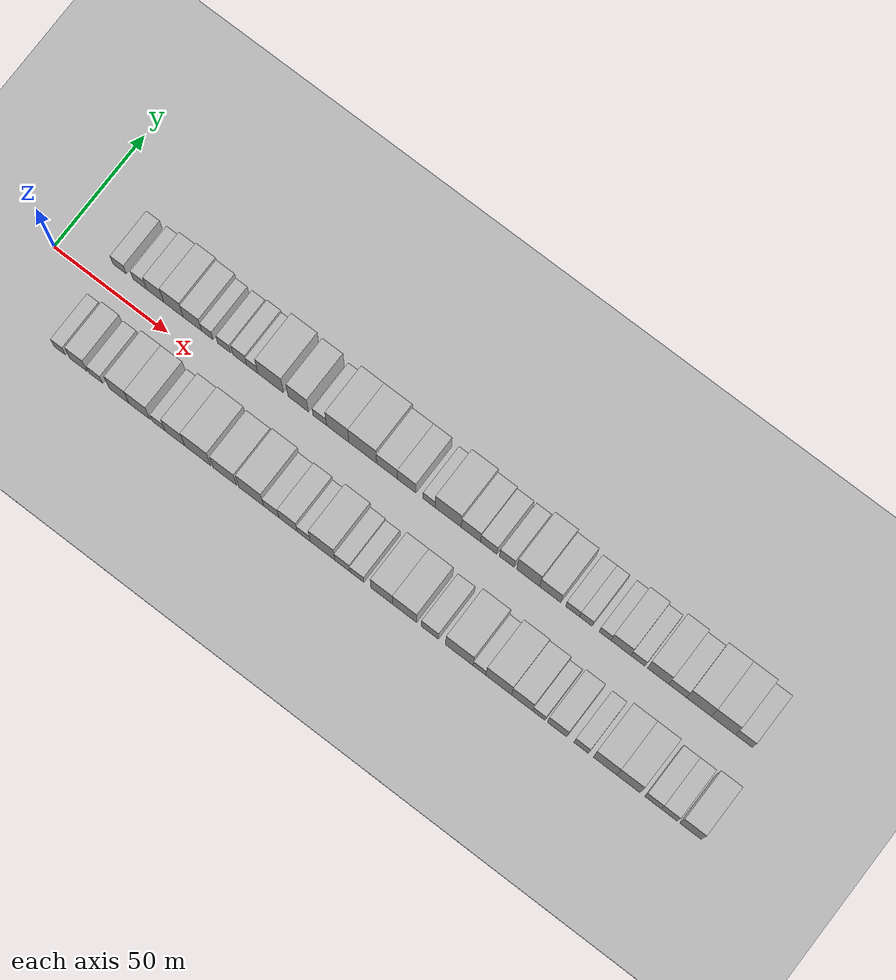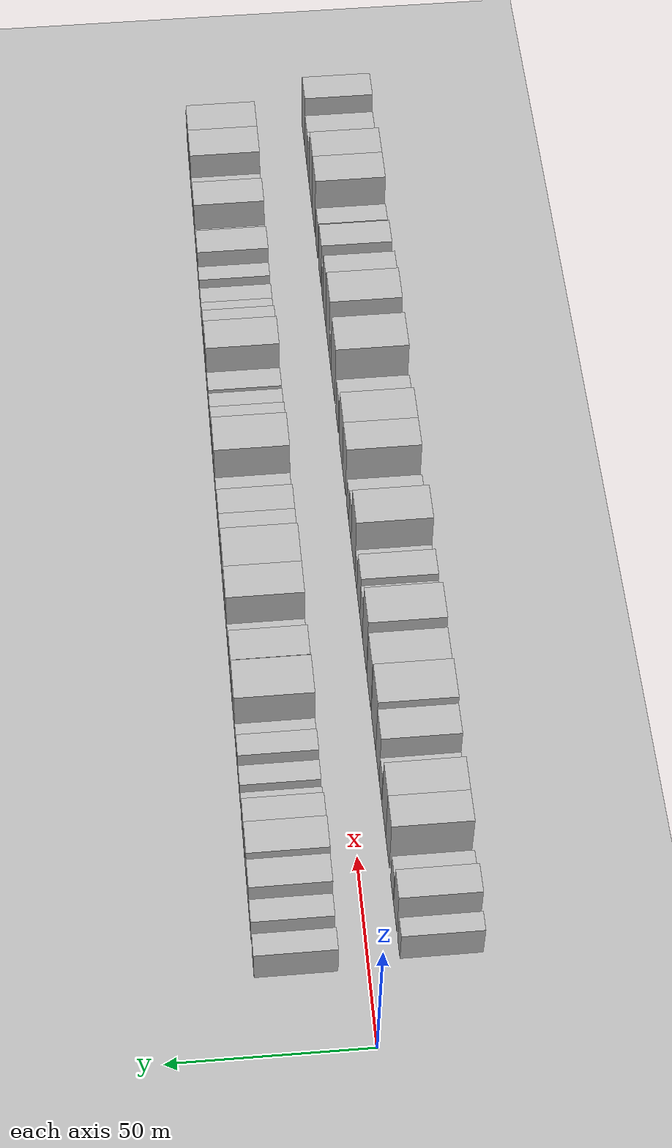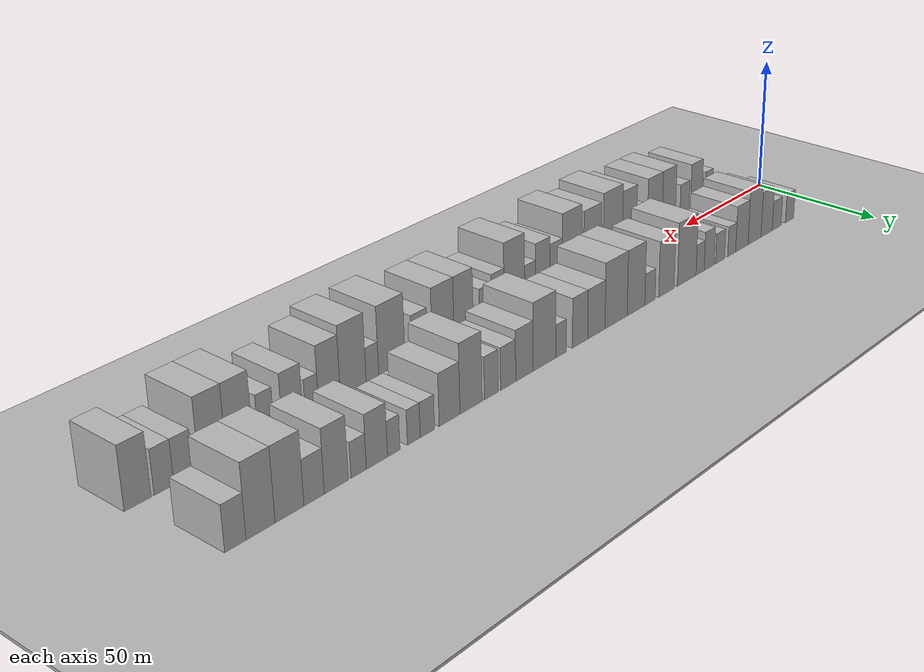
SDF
<?xml version="1.0" encoding="utf-8"?>

<sdf version="1.6">

   <world name="default">

      <gui fullscreen="0">

         <camera name="user_camera">

            <pose>-15 0 4.57585 0 0 0</pose>

            <view_controller>orbit</view_controller>

         </camera>

      </gui>

      <scene>

         <sky>

           <clouds>

             <speed>12</speed>

           </clouds>

         </sky>

         <ambient>0.4 0.4 0.4 1</ambient>

         <background>0.7 0.7 0.7 1</background>

         <shadows>1</shadows>

      </scene>

      <gravity>0 0 -9.8066</gravity>

      <magnetic_field>6e-06 2.3e-05 -4.2e-05</magnetic_field>

      <physics default="0" name="default_physics" type="ode">

         <ode>

            <solver>

               <type>quick</type>

               <iters>10</iters>

               <sor>1.0</sor>

               <use_dynamic_moi_rescaling>0</use_dynamic_moi_rescaling>

            </solver>

            <constraints>

               <cfm>0</cfm>

               <erp>0.2</erp>

               <contact_max_correcting_vel>100</contact_max_correcting_vel>

               <contact_surface_layer>0.001</contact_surface_layer>

            </constraints>

         </ode>

         <max_step_size>0.004</max_step_size>

         <real_time_factor>1</real_time_factor>

         <real_time_update_rate>250</real_time_update_rate>

      </physics>

      <light name="sun" type="directional">

         <cast_shadows>1</cast_shadows>

         <pose>0 0 10 0 0 0</pose>

         <diffuse>0.8 0.8 0.8 1</diffuse>

         <specular>0.2 0.2 0.2 1</specular>

         <attenuation>

            <range>1000</range>

            <constant>0.9</constant>

            <linear>0.01</linear>

            <quadratic>0.001</quadratic>

         </attenuation>

         <direction>-0.5 0.1 -0.9</direction>

      </light>

      <include>

         <name>ground_plane_1</name>

         <uri>model://HANNAS_ground_plane</uri>

         <pose>0 0 0  0 0 0</pose>

      </include>

      <include>

         <name>ground_plane_2</name>

         <uri>model://HANNAS_ground_plane</uri>

         <pose>100 0 0  0 0 0</pose>

      </include>

      <model name="building_1">

         <static>1</static>

         <pose frame="">22.8825 17.5000 0 0.000000 0.000000 1.570796</pose>

         <link name="link">

            <pose frame="">0 0 6.00 0 0 0</pose>

            <collision name="collision">

               <geometry>

                  <box>

                     <size>20.0000 5.7649 12.0000</size>

                  </box>

               </geometry>

               <max_contacts>10</max_contacts>

               <surface>

                  <contact>

                     <ode/>

                  </contact>

                  <bounce/>

                  <friction>

                     <torsional>

                        <ode/>

                     </torsional>

                     <ode/>

                  </friction>

               </surface>

            </collision>

            <visual name="visual">

               <cast_shadows>0</cast_shadows>

               <geometry>

                  <box>

                     <size>20.0000 5.7649 12.0000</size>

                  </box>

               </geometry>

               <material>

                  <script>

                     <uri>model://HANNAS_wall/materials/scripts</uri>

                     <uri>model://HANNAS_wall/materials/textures</uri>

                     <name>vrc/HANNAS_wall</name>

                  </script>

               </material>

            </visual>

            <self_collide>0</self_collide>

            <enable_wind>0</enable_wind>

            <kinematic>0</kinematic>

         </link>

      </model>

      <model name="building_2">

         <static>1</static>

         <pose frame="">31.7566 17.5000 0 0.000000 0.000000 1.570796</pose>

         <link name="link">

            <pose frame="">0 0 6.00 0 0 0</pose>

            <collision name="collision">

               <geometry>

                  <box>

                     <size>20.0000 5.9834 12.0000</size>

                  </box>

               </geometry>

               <max_contacts>10</max_contacts>

               <surface>

                  <contact>

                     <ode/>

                  </contact>

                  <bounce/>

                  <friction>

                     <torsional>

                        <ode/>

                     </torsional>

                     <ode/>

                  </friction>

               </surface>

            </collision>

            <visual name="visual">

               <cast_shadows>0</cast_shadows>

               <geometry>

                  <box>

                     <size>20.0000 5.9834 12.0000</size>

                  </box>

               </geometry>

               <material>

                  <script>

                     <uri>model://HANNAS_wall/materials/scripts</uri>

                     <uri>model://HANNAS_wall/materials/textures</uri>

                     <name>vrc/HANNAS_wall</name>

                  </script>

               </material>

            </visual>

            <self_collide>0</self_collide>

            <enable_wind>0</enable_wind>

            <kinematic>0</kinematic>

         </link>

      </model>

      <model name="building_3">

         <static>1</static>

         <pose frame="">38.5076 17.5000 0 0.000000 0.000000 1.570796</pose>

         <link name="link">

            <pose frame="">0 0 9.00 0 0 0</pose>

            <collision name="collision">

               <geometry>

                  <box>

                     <size>20.0000 7.5184 18.0000</size>

                  </box>

               </geometry>

               <max_contacts>10</max_contacts>

               <surface>

                  <contact>

                     <ode/>

                  </contact>

                  <bounce/>

                  <friction>

                     <torsional>

                        <ode/>

                     </torsional>

                     <ode/>

                  </friction>

               </surface>

            </collision>

            <visual name="visual">

               <cast_shadows>0</cast_shadows>

               <geometry>

                  <box>

                     <size>20.0000 7.5184 18.0000</size>

                  </box>

               </geometry>

               <material>

                  <script>

                     <uri>model://HANNAS_wall/materials/scripts</uri>

                     <uri>model://HANNAS_wall/materials/textures</uri>

                     <name>vrc/HANNAS_wall</name>

                  </script>

               </material>

            </visual>

            <self_collide>0</self_collide>

            <enable_wind>0</enable_wind>

            <kinematic>0</kinematic>

         </link>

      </model>

      <model name="building_4">

         <static>1</static>

         <pose frame="">46.5126 17.5000 0 0.000000 0.000000 1.570796</pose>

         <link name="link">

            <pose frame="">0 0 10.50 0 0 0</pose>

            <collision name="collision">

               <geometry>

                  <box>

                     <size>20.0000 8.4917 21.0000</size>

                  </box>

               </geometry>

               <max_contacts>10</max_contacts>

               <surface>

                  <contact>

                     <ode/>

                  </contact>

                  <bounce/>

                  <friction>

                     <torsional>

                        <ode/>

                     </torsional>

                     <ode/>

                  </friction>

               </surface>

            </collision>

            <visual name="visual">

               <cast_shadows>0</cast_shadows>

               <geometry>

                  <box>

                     <size>20.0000 8.4917 21.0000</size>

                  </box>

               </geometry>

               <material>

                  <script>

                     <uri>model://HANNAS_wall/materials/scripts</uri>

                     <uri>model://HANNAS_wall/materials/textures</uri>

                     <name>vrc/HANNAS_wall</name>

                  </script>

               </material>

            </visual>

            <self_collide>0</self_collide>

            <enable_wind>0</enable_wind>

            <kinematic>0</kinematic>

         </link>

      </model>

      <model name="building_5">

         <static>1</static>

         <pose frame="">54.7586 17.5000 0 0.000000 0.000000 1.570796</pose>

         <link name="link">

            <pose frame="">0 0 9.00 0 0 0</pose>

            <collision name="collision">

               <geometry>

                  <box>

                     <size>20.0000 8.0003 18.0000</size>

                  </box>

               </geometry>

               <max_contacts>10</max_contacts>

               <surface>

                  <contact>

                     <ode/>

                  </contact>

                  <bounce/>

                  <friction>

                     <torsional>

                        <ode/>

                     </torsional>

                     <ode/>

                  </friction>

               </surface>

            </collision>

            <visual name="visual">

               <cast_shadows>0</cast_shadows>

               <geometry>

                  <box>

                     <size>20.0000 8.0003 18.0000</size>

                  </box>

               </geometry>

               <material>

                  <script>

                     <uri>model://HANNAS_wall/materials/scripts</uri>

                     <uri>model://HANNAS_wall/materials/textures</uri>

                     <name>vrc/HANNAS_wall</name>

                  </script>

               </material>

            </visual>

            <self_collide>0</self_collide>

            <enable_wind>0</enable_wind>

            <kinematic>0</kinematic>

         </link>

      </model>

      <model name="building_6">

         <static>1</static>

         <pose frame="">61.2780 17.5000 0 0.000000 0.000000 1.570796</pose>

         <link name="link">

            <pose frame="">0 0 6.00 0 0 0</pose>

            <collision name="collision">

               <geometry>

                  <box>

                     <size>20.0000 5.0384 12.0000</size>

                  </box>

               </geometry>

               <max_contacts>10</max_contacts>

               <surface>

                  <contact>

                     <ode/>

                  </contact>

                  <bounce/>

                  <friction>

                     <torsional>

                        <ode/>

                     </torsional>

                     <ode/>

                  </friction>

               </surface>

            </collision>

            <visual name="visual">

               <cast_shadows>0</cast_shadows>

               <geometry>

                  <box>

                     <size>20.0000 5.0384 12.0000</size>

                  </box>

               </geometry>

               <material>

                  <script>

                     <uri>model://HANNAS_wall/materials/scripts</uri>

                     <uri>model://HANNAS_wall/materials/textures</uri>

                     <name>vrc/HANNAS_wall</name>

                  </script>

               </material>

            </visual>

            <self_collide>0</self_collide>

            <enable_wind>0</enable_wind>

            <kinematic>0</kinematic>

         </link>

      </model>

      <model name="building_7">

         <static>1</static>

         <pose frame="">68.5894 17.5000 0 0.000000 0.000000 1.570796</pose>

         <link name="link">

            <pose frame="">0 0 6.00 0 0 0</pose>

            <collision name="collision">

               <geometry>

                  <box>

                     <size>20.0000 5.5843 12.0000</size>

                  </box>

               </geometry>

               <max_contacts>10</max_contacts>

               <surface>

                  <contact>

                     <ode/>

                  </contact>

                  <bounce/>

                  <friction>

                     <torsional>

                        <ode/>

                     </torsional>

                     <ode/>

                  </friction>

               </surface>

            </collision>

            <visual name="visual">

               <cast_shadows>0</cast_shadows>

               <geometry>

                  <box>

                     <size>20.0000 5.5843 12.0000</size>

                  </box>

               </geometry>

               <material>

                  <script>

                     <uri>model://HANNAS_wall/materials/scripts</uri>

                     <uri>model://HANNAS_wall/materials/textures</uri>

                     <name>vrc/HANNAS_wall</name>

                  </script>

               </material>

            </visual>

            <self_collide>0</self_collide>

            <enable_wind>0</enable_wind>

            <kinematic>0</kinematic>

         </link>

      </model>

      <model name="building_8">

         <static>1</static>

         <pose frame="">75.3883 17.5000 0 0.000000 0.000000 1.570796</pose>

         <link name="link">

            <pose frame="">0 0 7.50 0 0 0</pose>

            <collision name="collision">

               <geometry>

                  <box>

                     <size>20.0000 6.0135 15.0000</size>

                  </box>

               </geometry>

               <max_contacts>10</max_contacts>

               <surface>

                  <contact>

                     <ode/>

                  </contact>

                  <bounce/>

                  <friction>

                     <torsional>

                        <ode/>

                     </torsional>

                     <ode/>

                  </friction>

               </surface>

            </collision>

            <visual name="visual">

               <cast_shadows>0</cast_shadows>

               <geometry>

                  <box>

                     <size>20.0000 6.0135 15.0000</size>

                  </box>

               </geometry>

               <material>

                  <script>

                     <uri>model://HANNAS_wall/materials/scripts</uri>

                     <uri>model://HANNAS_wall/materials/textures</uri>

                     <name>vrc/HANNAS_wall</name>

                  </script>

               </material>

            </visual>

            <self_collide>0</self_collide>

            <enable_wind>0</enable_wind>

            <kinematic>0</kinematic>

         </link>

      </model>

      <model name="building_9">

         <static>1</static>

         <pose frame="">80.8570 17.5000 0 0.000000 0.000000 1.570796</pose>

         <link name="link">

            <pose frame="">0 0 6.00 0 0 0</pose>

            <collision name="collision">

               <geometry>

                  <box>

                     <size>20.0000 4.9239 12.0000</size>

                  </box>

               </geometry>

               <max_contacts>10</max_contacts>

               <surface>

                  <contact>

                     <ode/>

                  </contact>

                  <bounce/>

                  <friction>

                     <torsional>

                        <ode/>

                     </torsional>

                     <ode/>

                  </friction>

               </surface>

            </collision>

            <visual name="visual">

               <cast_shadows>0</cast_shadows>

               <geometry>

                  <box>

                     <size>20.0000 4.9239 12.0000</size>

                  </box>

               </geometry>

               <material>

                  <script>

                     <uri>model://HANNAS_wall/materials/scripts</uri>

                     <uri>model://HANNAS_wall/materials/textures</uri>

                     <name>vrc/HANNAS_wall</name>

                  </script>

               </material>

            </visual>

            <self_collide>0</self_collide>

            <enable_wind>0</enable_wind>

            <kinematic>0</kinematic>

         </link>

      </model>

      <model name="building_10">

         <static>1</static>

         <pose frame="">88.8448 17.5000 0 0.000000 0.000000 1.570796</pose>

         <link name="link">

            <pose frame="">0 0 12.00 0 0 0</pose>

            <collision name="collision">

               <geometry>

                  <box>

                     <size>20.0000 11.0518 24.0000</size>

                  </box>

               </geometry>

               <max_contacts>10</max_contacts>

               <surface>

                  <contact>

                     <ode/>

                  </contact>

                  <bounce/>

                  <friction>

                     <torsional>

                        <ode/>

                     </torsional>

                     <ode/>

                  </friction>

               </surface>

            </collision>

            <visual name="visual">

               <cast_shadows>0</cast_shadows>

               <geometry>

                  <box>

                     <size>20.0000 11.0518 24.0000</size>

                  </box>

               </geometry>

               <material>

                  <script>

                     <uri>model://HANNAS_wall/materials/scripts</uri>

                     <uri>model://HANNAS_wall/materials/textures</uri>

                     <name>vrc/HANNAS_wall</name>

                  </script>

               </material>

            </visual>

            <self_collide>0</self_collide>

            <enable_wind>0</enable_wind>

            <kinematic>0</kinematic>

         </link>

      </model>

      <model name="building_11">

         <static>1</static>

         <pose frame="">100.7641 17.5000 0 0.000000 0.000000 1.570796</pose>

         <link name="link">

            <pose frame="">0 0 10.50 0 0 0</pose>

            <collision name="collision">

               <geometry>

                  <box>

                     <size>20.0000 8.7867 21.0000</size>

                  </box>

               </geometry>

               <max_contacts>10</max_contacts>

               <surface>

                  <contact>

                     <ode/>

                  </contact>

                  <bounce/>

                  <friction>

                     <torsional>

                        <ode/>

                     </torsional>

                     <ode/>

                  </friction>

               </surface>

            </collision>

            <visual name="visual">

               <cast_shadows>0</cast_shadows>

               <geometry>

                  <box>

                     <size>20.0000 8.7867 21.0000</size>

                  </box>

               </geometry>

               <material>

                  <script>

                     <uri>model://HANNAS_wall/materials/scripts</uri>

                     <uri>model://HANNAS_wall/materials/textures</uri>

                     <name>vrc/HANNAS_wall</name>

                  </script>

               </material>

            </visual>

            <self_collide>0</self_collide>

            <enable_wind>0</enable_wind>

            <kinematic>0</kinematic>

         </link>

      </model>

      <model name="building_12">

         <static>1</static>

         <pose frame="">110.0687 17.5000 0 0.000000 0.000000 1.570796</pose>

         <link name="link">

            <pose frame="">0 0 6.00 0 0 0</pose>

            <collision name="collision">

               <geometry>

                  <box>

                     <size>20.0000 5.8225 12.0000</size>

                  </box>

               </geometry>

               <max_contacts>10</max_contacts>

               <surface>

                  <contact>

                     <ode/>

                  </contact>

                  <bounce/>

                  <friction>

                     <torsional>

                        <ode/>

                     </torsional>

                     <ode/>

                  </friction>

               </surface>

            </collision>

            <visual name="visual">

               <cast_shadows>0</cast_shadows>

               <geometry>

                  <box>

                     <size>20.0000 5.8225 12.0000</size>

                  </box>

               </geometry>

               <material>

                  <script>

                     <uri>model://HANNAS_wall/materials/scripts</uri>

                     <uri>model://HANNAS_wall/materials/textures</uri>

                     <name>vrc/HANNAS_wall</name>

                  </script>

               </material>

            </visual>

            <self_collide>0</self_collide>

            <enable_wind>0</enable_wind>

            <kinematic>0</kinematic>

         </link>

      </model>

      <model name="building_13">

         <static>1</static>

         <pose frame="">117.8152 17.5000 0 0.000000 0.000000 1.570796</pose>

         <link name="link">

            <pose frame="">0 0 12.00 0 0 0</pose>

            <collision name="collision">

               <geometry>

                  <box>

                     <size>20.0000 9.6705 24.0000</size>

                  </box>

               </geometry>

               <max_contacts>10</max_contacts>

               <surface>

                  <contact>

                     <ode/>

                  </contact>

                  <bounce/>

                  <friction>

                     <torsional>

                        <ode/>

                     </torsional>

                     <ode/>

                  </friction>

               </surface>

            </collision>

            <visual name="visual">

               <cast_shadows>0</cast_shadows>

               <geometry>

                  <box>

                     <size>20.0000 9.6705 24.0000</size>

                  </box>

               </geometry>

               <material>

                  <script>

                     <uri>model://HANNAS_wall/materials/scripts</uri>

                     <uri>model://HANNAS_wall/materials/textures</uri>

                     <name>vrc/HANNAS_wall</name>

                  </script>

               </material>

            </visual>

            <self_collide>0</self_collide>

            <enable_wind>0</enable_wind>

            <kinematic>0</kinematic>

         </link>

      </model>

      <model name="building_14">

         <static>1</static>

         <pose frame="">128.5893 17.5000 0 0.000000 0.000000 1.570796</pose>

         <link name="link">

            <pose frame="">0 0 12.00 0 0 0</pose>

            <collision name="collision">

               <geometry>

                  <box>

                     <size>20.0000 11.8775 24.0000</size>

                  </box>

               </geometry>

               <max_contacts>10</max_contacts>

               <surface>

                  <contact>

                     <ode/>

                  </contact>

                  <bounce/>

                  <friction>

                     <torsional>

                        <ode/>

                     </torsional>

                     <ode/>

                  </friction>

               </surface>

            </collision>

            <visual name="visual">

               <cast_shadows>0</cast_shadows>

               <geometry>

                  <box>

                     <size>20.0000 11.8775 24.0000</size>

                  </box>

               </geometry>

               <material>

                  <script>

                     <uri>model://HANNAS_wall/materials/scripts</uri>

                     <uri>model://HANNAS_wall/materials/textures</uri>

                     <name>vrc/HANNAS_wall</name>

                  </script>

               </material>

            </visual>

            <self_collide>0</self_collide>

            <enable_wind>0</enable_wind>

            <kinematic>0</kinematic>

         </link>

      </model>

      <model name="building_15">

         <static>1</static>

         <pose frame="">139.0228 17.5000 0 0.000000 0.000000 1.570796</pose>

         <link name="link">

            <pose frame="">0 0 9.00 0 0 0</pose>

            <collision name="collision">

               <geometry>

                  <box>

                     <size>20.0000 8.9897 18.0000</size>

                  </box>

               </geometry>

               <max_contacts>10</max_contacts>

               <surface>

                  <contact>

                     <ode/>

                  </contact>

                  <bounce/>

                  <friction>

                     <torsional>

                        <ode/>

                     </torsional>

                     <ode/>

                  </friction>

               </surface>

            </collision>

            <visual name="visual">

               <cast_shadows>0</cast_shadows>

               <geometry>

                  <box>

                     <size>20.0000 8.9897 18.0000</size>

                  </box>

               </geometry>

               <material>

                  <script>

                     <uri>model://HANNAS_wall/materials/scripts</uri>

                     <uri>model://HANNAS_wall/materials/textures</uri>

                     <name>vrc/HANNAS_wall</name>

                  </script>

               </material>

            </visual>

            <self_collide>0</self_collide>

            <enable_wind>0</enable_wind>

            <kinematic>0</kinematic>

         </link>

      </model>

      <model name="building_16">

         <static>1</static>

         <pose frame="">147.4466 17.5000 0 0.000000 0.000000 1.570796</pose>

         <link name="link">

            <pose frame="">0 0 9.00 0 0 0</pose>

            <collision name="collision">

               <geometry>

                  <box>

                     <size>20.0000 7.8578 18.0000</size>

                  </box>

               </geometry>

               <max_contacts>10</max_contacts>

               <surface>

                  <contact>

                     <ode/>

                  </contact>

                  <bounce/>

                  <friction>

                     <torsional>

                        <ode/>

                     </torsional>

                     <ode/>

                  </friction>

               </surface>

            </collision>

            <visual name="visual">

               <cast_shadows>0</cast_shadows>

               <geometry>

                  <box>

                     <size>20.0000 7.8578 18.0000</size>

                  </box>

               </geometry>

               <material>

                  <script>

                     <uri>model://HANNAS_wall/materials/scripts</uri>

                     <uri>model://HANNAS_wall/materials/textures</uri>

                     <name>vrc/HANNAS_wall</name>

                  </script>

               </material>

            </visual>

            <self_collide>0</self_collide>

            <enable_wind>0</enable_wind>

            <kinematic>0</kinematic>

         </link>

      </model>

      <model name="building_17">

         <static>1</static>

         <pose frame="">156.9843 17.5000 0 0.000000 0.000000 1.570796</pose>

         <link name="link">

            <pose frame="">0 0 6.00 0 0 0</pose>

            <collision name="collision">

               <geometry>

                  <box>

                     <size>20.0000 5.2177 12.0000</size>

                  </box>

               </geometry>

               <max_contacts>10</max_contacts>

               <surface>

                  <contact>

                     <ode/>

                  </contact>

                  <bounce/>

                  <friction>

                     <torsional>

                        <ode/>

                     </torsional>

                     <ode/>

                  </friction>

               </surface>

            </collision>

            <visual name="visual">

               <cast_shadows>0</cast_shadows>

               <geometry>

                  <box>

                     <size>20.0000 5.2177 12.0000</size>

                  </box>

               </geometry>

               <material>

                  <script>

                     <uri>model://HANNAS_wall/materials/scripts</uri>

                     <uri>model://HANNAS_wall/materials/textures</uri>

                     <name>vrc/HANNAS_wall</name>

                  </script>

               </material>

            </visual>

            <self_collide>0</self_collide>

            <enable_wind>0</enable_wind>

            <kinematic>0</kinematic>

         </link>

      </model>

      <model name="building_18">

         <static>1</static>

         <pose frame="">165.1413 17.5000 0 0.000000 0.000000 1.570796</pose>

         <link name="link">

            <pose frame="">0 0 12.00 0 0 0</pose>

            <collision name="collision">

               <geometry>

                  <box>

                     <size>20.0000 11.0962 24.0000</size>

                  </box>

               </geometry>

               <max_contacts>10</max_contacts>

               <surface>

                  <contact>

                     <ode/>

                  </contact>

                  <bounce/>

                  <friction>

                     <torsional>

                        <ode/>

                     </torsional>

                     <ode/>

                  </friction>

               </surface>

            </collision>

            <visual name="visual">

               <cast_shadows>0</cast_shadows>

               <geometry>

                  <box>

                     <size>20.0000 11.0962 24.0000</size>

                  </box>

               </geometry>

               <material>

                  <script>

                     <uri>model://HANNAS_wall/materials/scripts</uri>

                     <uri>model://HANNAS_wall/materials/textures</uri>

                     <name>vrc/HANNAS_wall</name>

                  </script>

               </material>

            </visual>

            <self_collide>0</self_collide>

            <enable_wind>0</enable_wind>

            <kinematic>0</kinematic>

         </link>

      </model>

      <model name="building_19">

         <static>1</static>

         <pose frame="">174.8093 17.5000 0 0.000000 0.000000 1.570796</pose>

         <link name="link">

            <pose frame="">0 0 9.00 0 0 0</pose>

            <collision name="collision">

               <geometry>

                  <box>

                     <size>20.0000 8.2399 18.0000</size>

                  </box>

               </geometry>

               <max_contacts>10</max_contacts>

               <surface>

                  <contact>

                     <ode/>

                  </contact>

                  <bounce/>

                  <friction>

                     <torsional>

                        <ode/>

                     </torsional>

                     <ode/>

                  </friction>

               </surface>

            </collision>

            <visual name="visual">

               <cast_shadows>0</cast_shadows>

               <geometry>

                  <box>

                     <size>20.0000 8.2399 18.0000</size>

                  </box>

               </geometry>

               <material>

                  <script>

                     <uri>model://HANNAS_wall/materials/scripts</uri>

                     <uri>model://HANNAS_wall/materials/textures</uri>

                     <name>vrc/HANNAS_wall</name>

                  </script>

               </material>

            </visual>

            <self_collide>0</self_collide>

            <enable_wind>0</enable_wind>

            <kinematic>0</kinematic>

         </link>

      </model>

      <model name="building_20">

         <static>1</static>

         <pose frame="">182.4433 17.5000 0 0.000000 0.000000 1.570796</pose>

         <link name="link">

            <pose frame="">0 0 7.50 0 0 0</pose>

            <collision name="collision">

               <geometry>

                  <box>

                     <size>20.0000 7.0280 15.0000</size>

                  </box>

               </geometry>

               <max_contacts>10</max_contacts>

               <surface>

                  <contact>

                     <ode/>

                  </contact>

                  <bounce/>

                  <friction>

                     <torsional>

                        <ode/>

                     </torsional>

                     <ode/>

                  </friction>

               </surface>

            </collision>

            <visual name="visual">

               <cast_shadows>0</cast_shadows>

               <geometry>

                  <box>

                     <size>20.0000 7.0280 15.0000</size>

                  </box>

               </geometry>

               <material>

                  <script>

                     <uri>model://HANNAS_wall/materials/scripts</uri>

                     <uri>model://HANNAS_wall/materials/textures</uri>

                     <name>vrc/HANNAS_wall</name>

                  </script>

               </material>

            </visual>

            <self_collide>0</self_collide>

            <enable_wind>0</enable_wind>

            <kinematic>0</kinematic>

         </link>

      </model>

      <model name="building_21">

         <static>1</static>

         <pose frame="">190.1219 17.5000 0 0.000000 0.000000 1.570796</pose>

         <link name="link">

            <pose frame="">0 0 7.50 0 0 0</pose>

            <collision name="collision">

               <geometry>

                  <box>

                     <size>20.0000 6.3291 15.0000</size>

                  </box>

               </geometry>

               <max_contacts>10</max_contacts>

               <surface>

                  <contact>

                     <ode/>

                  </contact>

                  <bounce/>

                  <friction>

                     <torsional>

                        <ode/>

                     </torsional>

                     <ode/>

                  </friction>

               </surface>

            </collision>

            <visual name="visual">

               <cast_shadows>0</cast_shadows>

               <geometry>

                  <box>

                     <size>20.0000 6.3291 15.0000</size>

                  </box>

               </geometry>

               <material>

                  <script>

                     <uri>model://HANNAS_wall/materials/scripts</uri>

                     <uri>model://HANNAS_wall/materials/textures</uri>

                     <name>vrc/HANNAS_wall</name>

                  </script>

               </material>

            </visual>

            <self_collide>0</self_collide>

            <enable_wind>0</enable_wind>

            <kinematic>0</kinematic>

         </link>

      </model>

      <model name="building_22">

         <static>1</static>

         <pose frame="">199.1633 17.5000 0 0.000000 0.000000 1.570796</pose>

         <link name="link">

            <pose frame="">0 0 12.00 0 0 0</pose>

            <collision name="collision">

               <geometry>

                  <box>

                     <size>20.0000 9.7538 24.0000</size>

                  </box>

               </geometry>

               <max_contacts>10</max_contacts>

               <surface>

                  <contact>

                     <ode/>

                  </contact>

                  <bounce/>

                  <friction>

                     <torsional>

                        <ode/>

                     </torsional>

                     <ode/>

                  </friction>

               </surface>

            </collision>

            <visual name="visual">

               <cast_shadows>0</cast_shadows>

               <geometry>

                  <box>

                     <size>20.0000 9.7538 24.0000</size>

                  </box>

               </geometry>

               <material>

                  <script>

                     <uri>model://HANNAS_wall/materials/scripts</uri>

                     <uri>model://HANNAS_wall/materials/textures</uri>

                     <name>vrc/HANNAS_wall</name>

                  </script>

               </material>

            </visual>

            <self_collide>0</self_collide>

            <enable_wind>0</enable_wind>

            <kinematic>0</kinematic>

         </link>

      </model>

      <model name="building_23">

         <static>1</static>

         <pose frame="">208.5142 17.5000 0 0.000000 0.000000 1.570796</pose>

         <link name="link">

            <pose frame="">0 0 9.00 0 0 0</pose>

            <collision name="collision">

               <geometry>

                  <box>

                     <size>20.0000 8.9480 18.0000</size>

                  </box>

               </geometry>

               <max_contacts>10</max_contacts>

               <surface>

                  <contact>

                     <ode/>

                  </contact>

                  <bounce/>

                  <friction>

                     <torsional>

                        <ode/>

                     </torsional>

                     <ode/>

                  </friction>

               </surface>

            </collision>

            <visual name="visual">

               <cast_shadows>0</cast_shadows>

               <geometry>

                  <box>

                     <size>20.0000 8.9480 18.0000</size>

                  </box>

               </geometry>

               <material>

                  <script>

                     <uri>model://HANNAS_wall/materials/scripts</uri>

                     <uri>model://HANNAS_wall/materials/textures</uri>

                     <name>vrc/HANNAS_wall</name>

                  </script>

               </material>

            </visual>

            <self_collide>0</self_collide>

            <enable_wind>0</enable_wind>

            <kinematic>0</kinematic>

         </link>

      </model>

      <model name="building_24">

         <static>1</static>

         <pose frame="">217.9626 17.5000 0 0.000000 0.000000 1.570796</pose>

         <link name="link">

            <pose frame="">0 0 6.00 0 0 0</pose>

            <collision name="collision">

               <geometry>

                  <box>

                     <size>20.0000 5.9486 12.0000</size>

                  </box>

               </geometry>

               <max_contacts>10</max_contacts>

               <surface>

                  <contact>

                     <ode/>

                  </contact>

                  <bounce/>

                  <friction>

                     <torsional>

                        <ode/>

                     </torsional>

                     <ode/>

                  </friction>

               </surface>

            </collision>

            <visual name="visual">

               <cast_shadows>0</cast_shadows>

               <geometry>

                  <box>

                     <size>20.0000 5.9486 12.0000</size>

                  </box>

               </geometry>

               <material>

                  <script>

                     <uri>model://HANNAS_wall/materials/scripts</uri>

                     <uri>model://HANNAS_wall/materials/textures</uri>

                     <name>vrc/HANNAS_wall</name>

                  </script>

               </material>

            </visual>

            <self_collide>0</self_collide>

            <enable_wind>0</enable_wind>

            <kinematic>0</kinematic>

         </link>

      </model>

      <model name="building_25">

         <static>1</static>

         <pose frame="">223.5839 17.5000 0 0.000000 0.000000 1.570796</pose>

         <link name="link">

            <pose frame="">0 0 6.00 0 0 0</pose>

            <collision name="collision">

               <geometry>

                  <box>

                     <size>20.0000 5.2940 12.0000</size>

                  </box>

               </geometry>

               <max_contacts>10</max_contacts>

               <surface>

                  <contact>

                     <ode/>

                  </contact>

                  <bounce/>

                  <friction>

                     <torsional>

                        <ode/>

                     </torsional>

                     <ode/>

                  </friction>

               </surface>

            </collision>

            <visual name="visual">

               <cast_shadows>0</cast_shadows>

               <geometry>

                  <box>

                     <size>20.0000 5.2940 12.0000</size>

                  </box>

               </geometry>

               <material>

                  <script>

                     <uri>model://HANNAS_wall/materials/scripts</uri>

                     <uri>model://HANNAS_wall/materials/textures</uri>

                     <name>vrc/HANNAS_wall</name>

                  </script>

               </material>

            </visual>

            <self_collide>0</self_collide>

            <enable_wind>0</enable_wind>

            <kinematic>0</kinematic>

         </link>

      </model>

      <model name="building_26">

         <static>1</static>

         <pose frame="">231.7309 17.5000 0 0.000000 0.000000 1.570796</pose>

         <link name="link">

            <pose frame="">0 0 6.00 0 0 0</pose>

            <collision name="collision">

               <geometry>

                  <box>

                     <size>20.0000 5.0000 12.0000</size>

                  </box>

               </geometry>

               <max_contacts>10</max_contacts>

               <surface>

                  <contact>

                     <ode/>

                  </contact>

                  <bounce/>

                  <friction>

                     <torsional>

                        <ode/>

                     </torsional>

                     <ode/>

                  </friction>

               </surface>

            </collision>

            <visual name="visual">

               <cast_shadows>0</cast_shadows>

               <geometry>

                  <box>

                     <size>20.0000 5.0000 12.0000</size>

                  </box>

               </geometry>

               <material>

                  <script>

                     <uri>model://HANNAS_wall/materials/scripts</uri>

                     <uri>model://HANNAS_wall/materials/textures</uri>

                     <name>vrc/HANNAS_wall</name>

                  </script>

               </material>

            </visual>

            <self_collide>0</self_collide>

            <enable_wind>0</enable_wind>

            <kinematic>0</kinematic>

         </link>

      </model>

      <model name="building_27">

         <static>1</static>

         <pose frame="">238.4052 17.5000 0 0.000000 0.000000 1.570796</pose>

         <link name="link">

            <pose frame="">0 0 9.00 0 0 0</pose>

            <collision name="collision">

               <geometry>

                  <box>

                     <size>20.0000 8.3485 18.0000</size>

                  </box>

               </geometry>

               <max_contacts>10</max_contacts>

               <surface>

                  <contact>

                     <ode/>

                  </contact>

                  <bounce/>

                  <friction>

                     <torsional>

                        <ode/>

                     </torsional>

                     <ode/>

                  </friction>

               </surface>

            </collision>

            <visual name="visual">

               <cast_shadows>0</cast_shadows>

               <geometry>

                  <box>

                     <size>20.0000 8.3485 18.0000</size>

                  </box>

               </geometry>

               <material>

                  <script>

                     <uri>model://HANNAS_wall/materials/scripts</uri>

                     <uri>model://HANNAS_wall/materials/textures</uri>

                     <name>vrc/HANNAS_wall</name>

                  </script>

               </material>

            </visual>

            <self_collide>0</self_collide>

            <enable_wind>0</enable_wind>

            <kinematic>0</kinematic>

         </link>

      </model>

      <model name="building_28">

         <static>1</static>

         <pose frame="">245.5368 17.5000 0 0.000000 0.000000 1.570796</pose>

         <link name="link">

            <pose frame="">0 0 6.00 0 0 0</pose>

            <collision name="collision">

               <geometry>

                  <box>

                     <size>20.0000 5.9148 12.0000</size>

                  </box>

               </geometry>

               <max_contacts>10</max_contacts>

               <surface>

                  <contact>

                     <ode/>

                  </contact>

                  <bounce/>

                  <friction>

                     <torsional>

                        <ode/>

                     </torsional>

                     <ode/>

                  </friction>

               </surface>

            </collision>

            <visual name="visual">

               <cast_shadows>0</cast_shadows>

               <geometry>

                  <box>

                     <size>20.0000 5.9148 12.0000</size>

                  </box>

               </geometry>

               <material>

                  <script>

                     <uri>model://HANNAS_wall/materials/scripts</uri>

                     <uri>model://HANNAS_wall/materials/textures</uri>

                     <name>vrc/HANNAS_wall</name>

                  </script>

               </material>

            </visual>

            <self_collide>0</self_collide>

            <enable_wind>0</enable_wind>

            <kinematic>0</kinematic>

         </link>

      </model>

      <model name="building_29">

         <static>1</static>

         <pose frame="">253.9768 17.5000 0 0.000000 0.000000 1.570796</pose>

         <link name="link">

            <pose frame="">0 0 10.50 0 0 0</pose>

            <collision name="collision">

               <geometry>

                  <box>

                     <size>20.0000 8.9652 21.0000</size>

                  </box>

               </geometry>

               <max_contacts>10</max_contacts>

               <surface>

                  <contact>

                     <ode/>

                  </contact>

                  <bounce/>

                  <friction>

                     <torsional>

                        <ode/>

                     </torsional>

                     <ode/>

                  </friction>

               </surface>

            </collision>

            <visual name="visual">

               <cast_shadows>0</cast_shadows>

               <geometry>

                  <box>

                     <size>20.0000 8.9652 21.0000</size>

                  </box>

               </geometry>

               <material>

                  <script>

                     <uri>model://HANNAS_wall/materials/scripts</uri>

                     <uri>model://HANNAS_wall/materials/textures</uri>

                     <name>vrc/HANNAS_wall</name>

                  </script>

               </material>

            </visual>

            <self_collide>0</self_collide>

            <enable_wind>0</enable_wind>

            <kinematic>0</kinematic>

         </link>

      </model>

      <model name="building_30">

         <static>1</static>

         <pose frame="">262.1839 17.5000 0 0.000000 0.000000 1.570796</pose>

         <link name="link">

            <pose frame="">0 0 7.50 0 0 0</pose>

            <collision name="collision">

               <geometry>

                  <box>

                     <size>20.0000 7.4489 15.0000</size>

                  </box>

               </geometry>

               <max_contacts>10</max_contacts>

               <surface>

                  <contact>

                     <ode/>

                  </contact>

                  <bounce/>

                  <friction>

                     <torsional>

                        <ode/>

                     </torsional>

                     <ode/>

                  </friction>

               </surface>

            </collision>

            <visual name="visual">

               <cast_shadows>0</cast_shadows>

               <geometry>

                  <box>

                     <size>20.0000 7.4489 15.0000</size>

                  </box>

               </geometry>

               <material>

                  <script>

                     <uri>model://HANNAS_wall/materials/scripts</uri>

                     <uri>model://HANNAS_wall/materials/textures</uri>

                     <name>vrc/HANNAS_wall</name>

                  </script>

               </material>

            </visual>

            <self_collide>0</self_collide>

            <enable_wind>0</enable_wind>

            <kinematic>0</kinematic>

         </link>

      </model>

      <model name="building_31">

         <static>1</static>

         <pose frame="">271.0399 17.5000 0 0.000000 0.000000 1.570796</pose>

         <link name="link">

            <pose frame="">0 0 12.00 0 0 0</pose>

            <collision name="collision">

               <geometry>

                  <box>

                     <size>20.0000 10.2631 24.0000</size>

                  </box>

               </geometry>

               <max_contacts>10</max_contacts>

               <surface>

                  <contact>

                     <ode/>

                  </contact>

                  <bounce/>

                  <friction>

                     <torsional>

                        <ode/>

                     </torsional>

                     <ode/>

                  </friction>

               </surface>

            </collision>

            <visual name="visual">

               <cast_shadows>0</cast_shadows>

               <geometry>

                  <box>

                     <size>20.0000 10.2631 24.0000</size>

                  </box>

               </geometry>

               <material>

                  <script>

                     <uri>model://HANNAS_wall/materials/scripts</uri>

                     <uri>model://HANNAS_wall/materials/textures</uri>

                     <name>vrc/HANNAS_wall</name>

                  </script>

               </material>

            </visual>

            <self_collide>0</self_collide>

            <enable_wind>0</enable_wind>

            <kinematic>0</kinematic>

         </link>

      </model>

      <model name="building_32">

         <static>1</static>

         <pose frame="">281.1523 17.5000 0 0.000000 0.000000 1.570796</pose>

         <link name="link">

            <pose frame="">0 0 12.00 0 0 0</pose>

            <collision name="collision">

               <geometry>

                  <box>

                     <size>20.0000 9.9617 24.0000</size>

                  </box>

               </geometry>

               <max_contacts>10</max_contacts>

               <surface>

                  <contact>

                     <ode/>

                  </contact>

                  <bounce/>

                  <friction>

                     <torsional>

                        <ode/>

                     </torsional>

                     <ode/>

                  </friction>

               </surface>

            </collision>

            <visual name="visual">

               <cast_shadows>0</cast_shadows>

               <geometry>

                  <box>

                     <size>20.0000 9.9617 24.0000</size>

                  </box>

               </geometry>

               <material>

                  <script>

                     <uri>model://HANNAS_wall/materials/scripts</uri>

                     <uri>model://HANNAS_wall/materials/textures</uri>

                     <name>vrc/HANNAS_wall</name>

                  </script>

               </material>

            </visual>

            <self_collide>0</self_collide>

            <enable_wind>0</enable_wind>

            <kinematic>0</kinematic>

         </link>

      </model>

      <model name="building_33">

         <static>1</static>

         <pose frame="">289.7270 17.5000 0 0.000000 0.000000 1.570796</pose>

         <link name="link">

            <pose frame="">0 0 7.50 0 0 0</pose>

            <collision name="collision">

               <geometry>

                  <box>

                     <size>20.0000 7.1876 15.0000</size>

                  </box>

               </geometry>

               <max_contacts>10</max_contacts>

               <surface>

                  <contact>

                     <ode/>

                  </contact>

                  <bounce/>

                  <friction>

                     <torsional>

                        <ode/>

                     </torsional>

                     <ode/>

                  </friction>

               </surface>

            </collision>

            <visual name="visual">

               <cast_shadows>0</cast_shadows>

               <geometry>

                  <box>

                     <size>20.0000 7.1876 15.0000</size>

                  </box>

               </geometry>

               <material>

                  <script>

                     <uri>model://HANNAS_wall/materials/scripts</uri>

                     <uri>model://HANNAS_wall/materials/textures</uri>

                     <name>vrc/HANNAS_wall</name>

                  </script>

               </material>

            </visual>

            <self_collide>0</self_collide>

            <enable_wind>0</enable_wind>

            <kinematic>0</kinematic>

         </link>

      </model>

      <model name="building_34">

         <static>1</static>

         <pose frame="">24.4968 -17.5000 0 0.000000 0.000000 1.570796</pose>

         <link name="link">

            <pose frame="">0 0 6.00 0 0 0</pose>

            <collision name="collision">

               <geometry>

                  <box>

                     <size>20.0000 4.9936 12.0000</size>

                  </box>

               </geometry>

               <max_contacts>10</max_contacts>

               <surface>

                  <contact>

                     <ode/>

                  </contact>

                  <bounce/>

                  <friction>

                     <torsional>

                        <ode/>

                     </torsional>

                     <ode/>

                  </friction>

               </surface>

            </collision>

            <visual name="visual">

               <cast_shadows>0</cast_shadows>

               <geometry>

                  <box>

                     <size>20.0000 4.9936 12.0000</size>

                  </box>

               </geometry>

               <material>

                  <script>

                     <uri>model://HANNAS_wall/materials/scripts</uri>

                     <uri>model://HANNAS_wall/materials/textures</uri>

                     <name>vrc/HANNAS_wall</name>

                  </script>

               </material>

            </visual>

            <self_collide>0</self_collide>

            <enable_wind>0</enable_wind>

            <kinematic>0</kinematic>

         </link>

      </model>

      <model name="building_35">

         <static>1</static>

         <pose frame="">32.7701 -17.5000 0 0.000000 0.000000 1.570796</pose>

         <link name="link">

            <pose frame="">0 0 9.00 0 0 0</pose>

            <collision name="collision">

               <geometry>

                  <box>

                     <size>20.0000 7.5528 18.0000</size>

                  </box>

               </geometry>

               <max_contacts>10</max_contacts>

               <surface>

                  <contact>

                     <ode/>

                  </contact>

                  <bounce/>

                  <friction>

                     <torsional>

                        <ode/>

                     </torsional>

                     <ode/>

                  </friction>

               </surface>

            </collision>

            <visual name="visual">

               <cast_shadows>0</cast_shadows>

               <geometry>

                  <box>

                     <size>20.0000 7.5528 18.0000</size>

                  </box>

               </geometry>

               <material>

                  <script>

                     <uri>model://HANNAS_wall/materials/scripts</uri>

                     <uri>model://HANNAS_wall/materials/textures</uri>

                     <name>vrc/HANNAS_wall</name>

                  </script>

               </material>

            </visual>

            <self_collide>0</self_collide>

            <enable_wind>0</enable_wind>

            <kinematic>0</kinematic>

         </link>

      </model>

      <model name="building_36">

         <static>1</static>

         <pose frame="">40.4306 -17.5000 0 0.000000 0.000000 1.570796</pose>

         <link name="link">

            <pose frame="">0 0 6.00 0 0 0</pose>

            <collision name="collision">

               <geometry>

                  <box>

                     <size>20.0000 5.7682 12.0000</size>

                  </box>

               </geometry>

               <max_contacts>10</max_contacts>

               <surface>

                  <contact>

                     <ode/>

                  </contact>

                  <bounce/>

                  <friction>

                     <torsional>

                        <ode/>

                     </torsional>

                     <ode/>

                  </friction>

               </surface>

            </collision>

            <visual name="visual">

               <cast_shadows>0</cast_shadows>

               <geometry>

                  <box>

                     <size>20.0000 5.7682 12.0000</size>

                  </box>

               </geometry>

               <material>

                  <script>

                     <uri>model://HANNAS_wall/materials/scripts</uri>

                     <uri>model://HANNAS_wall/materials/textures</uri>

                     <name>vrc/HANNAS_wall</name>

                  </script>

               </material>

            </visual>

            <self_collide>0</self_collide>

            <enable_wind>0</enable_wind>

            <kinematic>0</kinematic>

         </link>

      </model>

      <model name="building_37">

         <static>1</static>

         <pose frame="">50.5580 -17.5000 0 0.000000 0.000000 1.570796</pose>

         <link name="link">

            <pose frame="">0 0 10.50 0 0 0</pose>

            <collision name="collision">

               <geometry>

                  <box>

                     <size>20.0000 8.4867 21.0000</size>

                  </box>

               </geometry>

               <max_contacts>10</max_contacts>

               <surface>

                  <contact>

                     <ode/>

                  </contact>

                  <bounce/>

                  <friction>

                     <torsional>

                        <ode/>

                     </torsional>

                     <ode/>

                  </friction>

               </surface>

            </collision>

            <visual name="visual">

               <cast_shadows>0</cast_shadows>

               <geometry>

                  <box>

                     <size>20.0000 8.4867 21.0000</size>

                  </box>

               </geometry>

               <material>

                  <script>

                     <uri>model://HANNAS_wall/materials/scripts</uri>

                     <uri>model://HANNAS_wall/materials/textures</uri>

                     <name>vrc/HANNAS_wall</name>

                  </script>

               </material>

            </visual>

            <self_collide>0</self_collide>

            <enable_wind>0</enable_wind>

            <kinematic>0</kinematic>

         </link>

      </model>

      <model name="building_38">

         <static>1</static>

         <pose frame="">59.3773 -17.5000 0 0.000000 0.000000 1.570796</pose>

         <link name="link">

            <pose frame="">0 0 10.50 0 0 0</pose>

            <collision name="collision">

               <geometry>

                  <box>

                     <size>20.0000 9.1519 21.0000</size>

                  </box>

               </geometry>

               <max_contacts>10</max_contacts>

               <surface>

                  <contact>

                     <ode/>

                  </contact>

                  <bounce/>

                  <friction>

                     <torsional>

                        <ode/>

                     </torsional>

                     <ode/>

                  </friction>

               </surface>

            </collision>

            <visual name="visual">

               <cast_shadows>0</cast_shadows>

               <geometry>

                  <box>

                     <size>20.0000 9.1519 21.0000</size>

                  </box>

               </geometry>

               <material>

                  <script>

                     <uri>model://HANNAS_wall/materials/scripts</uri>

                     <uri>model://HANNAS_wall/materials/textures</uri>

                     <name>vrc/HANNAS_wall</name>

                  </script>

               </material>

            </visual>

            <self_collide>0</self_collide>

            <enable_wind>0</enable_wind>

            <kinematic>0</kinematic>

         </link>

      </model>

      <model name="building_39">

         <static>1</static>

         <pose frame="">67.7289 -17.5000 0 0.000000 0.000000 1.570796</pose>

         <link name="link">

            <pose frame="">0 0 6.00 0 0 0</pose>

            <collision name="collision">

               <geometry>

                  <box>

                     <size>20.0000 5.5512 12.0000</size>

                  </box>

               </geometry>

               <max_contacts>10</max_contacts>

               <surface>

                  <contact>

                     <ode/>

                  </contact>

                  <bounce/>

                  <friction>

                     <torsional>

                        <ode/>

                     </torsional>

                     <ode/>

                  </friction>

               </surface>

            </collision>

            <visual name="visual">

               <cast_shadows>0</cast_shadows>

               <geometry>

                  <box>

                     <size>20.0000 5.5512 12.0000</size>

                  </box>

               </geometry>

               <material>

                  <script>

                     <uri>model://HANNAS_wall/materials/scripts</uri>

                     <uri>model://HANNAS_wall/materials/textures</uri>

                     <name>vrc/HANNAS_wall</name>

                  </script>

               </material>

            </visual>

            <self_collide>0</self_collide>

            <enable_wind>0</enable_wind>

            <kinematic>0</kinematic>

         </link>

      </model>

      <model name="building_40">

         <static>1</static>

         <pose frame="">74.7771 -17.5000 0 0.000000 0.000000 1.570796</pose>

         <link name="link">

            <pose frame="">0 0 10.50 0 0 0</pose>

            <collision name="collision">

               <geometry>

                  <box>

                     <size>20.0000 8.5453 21.0000</size>

                  </box>

               </geometry>

               <max_contacts>10</max_contacts>

               <surface>

                  <contact>

                     <ode/>

                  </contact>

                  <bounce/>

                  <friction>

                     <torsional>

                        <ode/>

                     </torsional>

                     <ode/>

                  </friction>

               </surface>

            </collision>

            <visual name="visual">

               <cast_shadows>0</cast_shadows>

               <geometry>

                  <box>

                     <size>20.0000 8.5453 21.0000</size>

                  </box>

               </geometry>

               <material>

                  <script>

                     <uri>model://HANNAS_wall/materials/scripts</uri>

                     <uri>model://HANNAS_wall/materials/textures</uri>

                     <name>vrc/HANNAS_wall</name>

                  </script>

               </material>

            </visual>

            <self_collide>0</self_collide>

            <enable_wind>0</enable_wind>

            <kinematic>0</kinematic>

         </link>

      </model>

      <model name="building_41">

         <static>1</static>

         <pose frame="">84.6604 -17.5000 0 0.000000 0.000000 1.570796</pose>

         <link name="link">

            <pose frame="">0 0 12.00 0 0 0</pose>

            <collision name="collision">

               <geometry>

                  <box>

                     <size>20.0000 11.2213 24.0000</size>

                  </box>

               </geometry>

               <max_contacts>10</max_contacts>

               <surface>

                  <contact>

                     <ode/>

                  </contact>

                  <bounce/>

                  <friction>

                     <torsional>

                        <ode/>

                     </torsional>

                     <ode/>

                  </friction>

               </surface>

            </collision>

            <visual name="visual">

               <cast_shadows>0</cast_shadows>

               <geometry>

                  <box>

                     <size>20.0000 11.2213 24.0000</size>

                  </box>

               </geometry>

               <material>

                  <script>

                     <uri>model://HANNAS_wall/materials/scripts</uri>

                     <uri>model://HANNAS_wall/materials/textures</uri>

                     <name>vrc/HANNAS_wall</name>

                  </script>

               </material>

            </visual>

            <self_collide>0</self_collide>

            <enable_wind>0</enable_wind>

            <kinematic>0</kinematic>

         </link>

      </model>

      <model name="building_42">

         <static>1</static>

         <pose frame="">96.3572 -17.5000 0 0.000000 0.000000 1.570796</pose>

         <link name="link">

            <pose frame="">0 0 10.50 0 0 0</pose>

            <collision name="collision">

               <geometry>

                  <box>

                     <size>20.0000 10.1722 21.0000</size>

                  </box>

               </geometry>

               <max_contacts>10</max_contacts>

               <surface>

                  <contact>

                     <ode/>

                  </contact>

                  <bounce/>

                  <friction>

                     <torsional>

                        <ode/>

                     </torsional>

                     <ode/>

                  </friction>

               </surface>

            </collision>

            <visual name="visual">

               <cast_shadows>0</cast_shadows>

               <geometry>

                  <box>

                     <size>20.0000 10.1722 21.0000</size>

                  </box>

               </geometry>

               <material>

                  <script>

                     <uri>model://HANNAS_wall/materials/scripts</uri>

                     <uri>model://HANNAS_wall/materials/textures</uri>

                     <name>vrc/HANNAS_wall</name>

                  </script>

               </material>

            </visual>

            <self_collide>0</self_collide>

            <enable_wind>0</enable_wind>

            <kinematic>0</kinematic>

         </link>

      </model>

      <model name="building_43">

         <static>1</static>

         <pose frame="">107.7852 -17.5000 0 0.000000 0.000000 1.570796</pose>

         <link name="link">

            <pose frame="">0 0 12.00 0 0 0</pose>

            <collision name="collision">

               <geometry>

                  <box>

                     <size>20.0000 10.6839 24.0000</size>

                  </box>

               </geometry>

               <max_contacts>10</max_contacts>

               <surface>

                  <contact>

                     <ode/>

                  </contact>

                  <bounce/>

                  <friction>

                     <torsional>

                        <ode/>

                     </torsional>

                     <ode/>

                  </friction>

               </surface>

            </collision>

            <visual name="visual">

               <cast_shadows>0</cast_shadows>

               <geometry>

                  <box>

                     <size>20.0000 10.6839 24.0000</size>

                  </box>

               </geometry>

               <material>

                  <script>

                     <uri>model://HANNAS_wall/materials/scripts</uri>

                     <uri>model://HANNAS_wall/materials/textures</uri>

                     <name>vrc/HANNAS_wall</name>

                  </script>

               </material>

            </visual>

            <self_collide>0</self_collide>

            <enable_wind>0</enable_wind>

            <kinematic>0</kinematic>

         </link>

      </model>

      <model name="building_44">

         <static>1</static>

         <pose frame="">116.4331 -17.5000 0 0.000000 0.000000 1.570796</pose>

         <link name="link">

            <pose frame="">0 0 7.50 0 0 0</pose>

            <collision name="collision">

               <geometry>

                  <box>

                     <size>20.0000 6.6119 15.0000</size>

                  </box>

               </geometry>

               <max_contacts>10</max_contacts>

               <surface>

                  <contact>

                     <ode/>

                  </contact>

                  <bounce/>

                  <friction>

                     <torsional>

                        <ode/>

                     </torsional>

                     <ode/>

                  </friction>

               </surface>

            </collision>

            <visual name="visual">

               <cast_shadows>0</cast_shadows>

               <geometry>

                  <box>

                     <size>20.0000 6.6119 15.0000</size>

                  </box>

               </geometry>

               <material>

                  <script>

                     <uri>model://HANNAS_wall/materials/scripts</uri>

                     <uri>model://HANNAS_wall/materials/textures</uri>

                     <name>vrc/HANNAS_wall</name>

                  </script>

               </material>

            </visual>

            <self_collide>0</self_collide>

            <enable_wind>0</enable_wind>

            <kinematic>0</kinematic>

         </link>

      </model>

      <model name="building_45">

         <static>1</static>

         <pose frame="">123.6493 -17.5000 0 0.000000 0.000000 1.570796</pose>

         <link name="link">

            <pose frame="">0 0 9.00 0 0 0</pose>

            <collision name="collision">

               <geometry>

                  <box>

                     <size>20.0000 7.8205 18.0000</size>

                  </box>

               </geometry>

               <max_contacts>10</max_contacts>

               <surface>

                  <contact>

                     <ode/>

                  </contact>

                  <bounce/>

                  <friction>

                     <torsional>

                        <ode/>

                     </torsional>

                     <ode/>

                  </friction>

               </surface>

            </collision>

            <visual name="visual">

               <cast_shadows>0</cast_shadows>

               <geometry>

                  <box>

                     <size>20.0000 7.8205 18.0000</size>

                  </box>

               </geometry>

               <material>

                  <script>

                     <uri>model://HANNAS_wall/materials/scripts</uri>

                     <uri>model://HANNAS_wall/materials/textures</uri>

                     <name>vrc/HANNAS_wall</name>

                  </script>

               </material>

            </visual>

            <self_collide>0</self_collide>

            <enable_wind>0</enable_wind>

            <kinematic>0</kinematic>

         </link>

      </model>

      <model name="building_46">

         <static>1</static>

         <pose frame="">130.3463 -17.5000 0 0.000000 0.000000 1.570796</pose>

         <link name="link">

            <pose frame="">0 0 6.00 0 0 0</pose>

            <collision name="collision">

               <geometry>

                  <box>

                     <size>20.0000 5.5735 12.0000</size>

                  </box>

               </geometry>

               <max_contacts>10</max_contacts>

               <surface>

                  <contact>

                     <ode/>

                  </contact>

                  <bounce/>

                  <friction>

                     <torsional>

                        <ode/>

                     </torsional>

                     <ode/>

                  </friction>

               </surface>

            </collision>

            <visual name="visual">

               <cast_shadows>0</cast_shadows>

               <geometry>

                  <box>

                     <size>20.0000 5.5735 12.0000</size>

                  </box>

               </geometry>

               <material>

                  <script>

                     <uri>model://HANNAS_wall/materials/scripts</uri>

                     <uri>model://HANNAS_wall/materials/textures</uri>

                     <name>vrc/HANNAS_wall</name>

                  </script>

               </material>

            </visual>

            <self_collide>0</self_collide>

            <enable_wind>0</enable_wind>

            <kinematic>0</kinematic>

         </link>

      </model>

      <model name="building_47">

         <static>1</static>

         <pose frame="">138.4124 -17.5000 0 0.000000 0.000000 1.570796</pose>

         <link name="link">

            <pose frame="">0 0 12.00 0 0 0</pose>

            <collision name="collision">

               <geometry>

                  <box>

                     <size>20.0000 10.5587 24.0000</size>

                  </box>

               </geometry>

               <max_contacts>10</max_contacts>

               <surface>

                  <contact>

                     <ode/>

                  </contact>

                  <bounce/>

                  <friction>

                     <torsional>

                        <ode/>

                     </torsional>

                     <ode/>

                  </friction>

               </surface>

            </collision>

            <visual name="visual">

               <cast_shadows>0</cast_shadows>

               <geometry>

                  <box>

                     <size>20.0000 10.5587 24.0000</size>

                  </box>

               </geometry>

               <material>

                  <script>

                     <uri>model://HANNAS_wall/materials/scripts</uri>

                     <uri>model://HANNAS_wall/materials/textures</uri>

                     <name>vrc/HANNAS_wall</name>

                  </script>

               </material>

            </visual>

            <self_collide>0</self_collide>

            <enable_wind>0</enable_wind>

            <kinematic>0</kinematic>

         </link>

      </model>

      <model name="building_48">

         <static>1</static>

         <pose frame="">146.8838 -17.5000 0 0.000000 0.000000 1.570796</pose>

         <link name="link">

            <pose frame="">0 0 7.50 0 0 0</pose>

            <collision name="collision">

               <geometry>

                  <box>

                     <size>20.0000 6.3841 15.0000</size>

                  </box>

               </geometry>

               <max_contacts>10</max_contacts>

               <surface>

                  <contact>

                     <ode/>

                  </contact>

                  <bounce/>

                  <friction>

                     <torsional>

                        <ode/>

                     </torsional>

                     <ode/>

                  </friction>

               </surface>

            </collision>

            <visual name="visual">

               <cast_shadows>0</cast_shadows>

               <geometry>

                  <box>

                     <size>20.0000 6.3841 15.0000</size>

                  </box>

               </geometry>

               <material>

                  <script>

                     <uri>model://HANNAS_wall/materials/scripts</uri>

                     <uri>model://HANNAS_wall/materials/textures</uri>

                     <name>vrc/HANNAS_wall</name>

                  </script>

               </material>

            </visual>

            <self_collide>0</self_collide>

            <enable_wind>0</enable_wind>

            <kinematic>0</kinematic>

         </link>

      </model>

      <model name="building_49">

         <static>1</static>

         <pose frame="">153.0710 -17.5000 0 0.000000 0.000000 1.570796</pose>

         <link name="link">

            <pose frame="">0 0 6.00 0 0 0</pose>

            <collision name="collision">

               <geometry>

                  <box>

                     <size>20.0000 5.9902 12.0000</size>

                  </box>

               </geometry>

               <max_contacts>10</max_contacts>

               <surface>

                  <contact>

                     <ode/>

                  </contact>

                  <bounce/>

                  <friction>

                     <torsional>

                        <ode/>

                     </torsional>

                     <ode/>

                  </friction>

               </surface>

            </collision>

            <visual name="visual">

               <cast_shadows>0</cast_shadows>

               <geometry>

                  <box>

                     <size>20.0000 5.9902 12.0000</size>

                  </box>

               </geometry>

               <material>

                  <script>

                     <uri>model://HANNAS_wall/materials/scripts</uri>

                     <uri>model://HANNAS_wall/materials/textures</uri>

                     <name>vrc/HANNAS_wall</name>

                  </script>

               </material>

            </visual>

            <self_collide>0</self_collide>

            <enable_wind>0</enable_wind>

            <kinematic>0</kinematic>

         </link>

      </model>

      <model name="building_50">

         <static>1</static>

         <pose frame="">163.6697 -17.5000 0 0.000000 0.000000 1.570796</pose>

         <link name="link">

            <pose frame="">0 0 10.50 0 0 0</pose>

            <collision name="collision">

               <geometry>

                  <box>

                     <size>20.0000 9.2074 21.0000</size>

                  </box>

               </geometry>

               <max_contacts>10</max_contacts>

               <surface>

                  <contact>

                     <ode/>

                  </contact>

                  <bounce/>

                  <friction>

                     <torsional>

                        <ode/>

                     </torsional>

                     <ode/>

                  </friction>

               </surface>

            </collision>

            <visual name="visual">

               <cast_shadows>0</cast_shadows>

               <geometry>

                  <box>

                     <size>20.0000 9.2074 21.0000</size>

                  </box>

               </geometry>

               <material>

                  <script>

                     <uri>model://HANNAS_wall/materials/scripts</uri>

                     <uri>model://HANNAS_wall/materials/textures</uri>

                     <name>vrc/HANNAS_wall</name>

                  </script>

               </material>

            </visual>

            <self_collide>0</self_collide>

            <enable_wind>0</enable_wind>

            <kinematic>0</kinematic>

         </link>

      </model>

      <model name="building_51">

         <static>1</static>

         <pose frame="">173.3958 -17.5000 0 0.000000 0.000000 1.570796</pose>

         <link name="link">

            <pose frame="">0 0 10.50 0 0 0</pose>

            <collision name="collision">

               <geometry>

                  <box>

                     <size>20.0000 10.2447 21.0000</size>

                  </box>

               </geometry>

               <max_contacts>10</max_contacts>

               <surface>

                  <contact>

                     <ode/>

                  </contact>

                  <bounce/>

                  <friction>

                     <torsional>

                        <ode/>

                     </torsional>

                     <ode/>

                  </friction>

               </surface>

            </collision>

            <visual name="visual">

               <cast_shadows>0</cast_shadows>

               <geometry>

                  <box>

                     <size>20.0000 10.2447 21.0000</size>

                  </box>

               </geometry>

               <material>

                  <script>

                     <uri>model://HANNAS_wall/materials/scripts</uri>

                     <uri>model://HANNAS_wall/materials/textures</uri>

                     <name>vrc/HANNAS_wall</name>

                  </script>

               </material>

            </visual>

            <self_collide>0</self_collide>

            <enable_wind>0</enable_wind>

            <kinematic>0</kinematic>

         </link>

      </model>

      <model name="building_52">

         <static>1</static>

         <pose frame="">184.1411 -17.5000 0 0.000000 0.000000 1.570796</pose>

         <link name="link">

            <pose frame="">0 0 7.50 0 0 0</pose>

            <collision name="collision">

               <geometry>

                  <box>

                     <size>20.0000 7.2460 15.0000</size>

                  </box>

               </geometry>

               <max_contacts>10</max_contacts>

               <surface>

                  <contact>

                     <ode/>

                  </contact>

                  <bounce/>

                  <friction>

                     <torsional>

                        <ode/>

                     </torsional>

                     <ode/>

                  </friction>

               </surface>

            </collision>

            <visual name="visual">

               <cast_shadows>0</cast_shadows>

               <geometry>

                  <box>

                     <size>20.0000 7.2460 15.0000</size>

                  </box>

               </geometry>

               <material>

                  <script>

                     <uri>model://HANNAS_wall/materials/scripts</uri>

                     <uri>model://HANNAS_wall/materials/textures</uri>

                     <name>vrc/HANNAS_wall</name>

                  </script>

               </material>

            </visual>

            <self_collide>0</self_collide>

            <enable_wind>0</enable_wind>

            <kinematic>0</kinematic>

         </link>

      </model>

      <model name="building_53">

         <static>1</static>

         <pose frame="">196.5894 -17.5000 0 0.000000 0.000000 1.570796</pose>

         <link name="link">

            <pose frame="">0 0 12.00 0 0 0</pose>

            <collision name="collision">

               <geometry>

                  <box>

                     <size>20.0000 11.6504 24.0000</size>

                  </box>

               </geometry>

               <max_contacts>10</max_contacts>

               <surface>

                  <contact>

                     <ode/>

                  </contact>

                  <bounce/>

                  <friction>

                     <torsional>

                        <ode/>

                     </torsional>

                     <ode/>

                  </friction>

               </surface>

            </collision>

            <visual name="visual">

               <cast_shadows>0</cast_shadows>

               <geometry>

                  <box>

                     <size>20.0000 11.6504 24.0000</size>

                  </box>

               </geometry>

               <material>

                  <script>

                     <uri>model://HANNAS_wall/materials/scripts</uri>

                     <uri>model://HANNAS_wall/materials/textures</uri>

                     <name>vrc/HANNAS_wall</name>

                  </script>

               </material>

            </visual>

            <self_collide>0</self_collide>

            <enable_wind>0</enable_wind>

            <kinematic>0</kinematic>

         </link>

      </model>

      <model name="building_54">

         <static>1</static>

         <pose frame="">205.1087 -17.5000 0 0.000000 0.000000 1.570796</pose>

         <link name="link">

            <pose frame="">0 0 6.00 0 0 0</pose>

            <collision name="collision">

               <geometry>

                  <box>

                     <size>20.0000 5.3881 12.0000</size>

                  </box>

               </geometry>

               <max_contacts>10</max_contacts>

               <surface>

                  <contact>

                     <ode/>

                  </contact>

                  <bounce/>

                  <friction>

                     <torsional>

                        <ode/>

                     </torsional>

                     <ode/>

                  </friction>

               </surface>

            </collision>

            <visual name="visual">

               <cast_shadows>0</cast_shadows>

               <geometry>

                  <box>

                     <size>20.0000 5.3881 12.0000</size>

                  </box>

               </geometry>

               <material>

                  <script>

                     <uri>model://HANNAS_wall/materials/scripts</uri>

                     <uri>model://HANNAS_wall/materials/textures</uri>

                     <name>vrc/HANNAS_wall</name>

                  </script>

               </material>

            </visual>

            <self_collide>0</self_collide>

            <enable_wind>0</enable_wind>

            <kinematic>0</kinematic>

         </link>

      </model>

      <model name="building_55">

         <static>1</static>

         <pose frame="">213.2072 -17.5000 0 0.000000 0.000000 1.570796</pose>

         <link name="link">

            <pose frame="">0 0 12.00 0 0 0</pose>

            <collision name="collision">

               <geometry>

                  <box>

                     <size>20.0000 10.8089 24.0000</size>

                  </box>

               </geometry>

               <max_contacts>10</max_contacts>

               <surface>

                  <contact>

                     <ode/>

                  </contact>

                  <bounce/>

                  <friction>

                     <torsional>

                        <ode/>

                     </torsional>

                     <ode/>

                  </friction>

               </surface>

            </collision>

            <visual name="visual">

               <cast_shadows>0</cast_shadows>

               <geometry>

                  <box>

                     <size>20.0000 10.8089 24.0000</size>

                  </box>

               </geometry>

               <material>

                  <script>

                     <uri>model://HANNAS_wall/materials/scripts</uri>

                     <uri>model://HANNAS_wall/materials/textures</uri>

                     <name>vrc/HANNAS_wall</name>

                  </script>

               </material>

            </visual>

            <self_collide>0</self_collide>

            <enable_wind>0</enable_wind>

            <kinematic>0</kinematic>

         </link>

      </model>

      <model name="building_56">

         <static>1</static>

         <pose frame="">223.0552 -17.5000 0 0.000000 0.000000 1.570796</pose>

         <link name="link">

            <pose frame="">0 0 10.50 0 0 0</pose>

            <collision name="collision">

               <geometry>

                  <box>

                     <size>20.0000 8.8871 21.0000</size>

                  </box>

               </geometry>

               <max_contacts>10</max_contacts>

               <surface>

                  <contact>

                     <ode/>

                  </contact>

                  <bounce/>

                  <friction>

                     <torsional>

                        <ode/>

                     </torsional>

                     <ode/>

                  </friction>

               </surface>

            </collision>

            <visual name="visual">

               <cast_shadows>0</cast_shadows>

               <geometry>

                  <box>

                     <size>20.0000 8.8871 21.0000</size>

                  </box>

               </geometry>

               <material>

                  <script>

                     <uri>model://HANNAS_wall/materials/scripts</uri>

                     <uri>model://HANNAS_wall/materials/textures</uri>

                     <name>vrc/HANNAS_wall</name>

                  </script>

               </material>

            </visual>

            <self_collide>0</self_collide>

            <enable_wind>0</enable_wind>

            <kinematic>0</kinematic>

         </link>

      </model>

      <model name="building_57">

         <static>1</static>

         <pose frame="">230.1291 -17.5000 0 0.000000 0.000000 1.570796</pose>

         <link name="link">

            <pose frame="">0 0 6.00 0 0 0</pose>

            <collision name="collision">

               <geometry>

                  <box>

                     <size>20.0000 5.2607 12.0000</size>

                  </box>

               </geometry>

               <max_contacts>10</max_contacts>

               <surface>

                  <contact>

                     <ode/>

                  </contact>

                  <bounce/>

                  <friction>

                     <torsional>

                        <ode/>

                     </torsional>

                     <ode/>

                  </friction>

               </surface>

            </collision>

            <visual name="visual">

               <cast_shadows>0</cast_shadows>

               <geometry>

                  <box>

                     <size>20.0000 5.2607 12.0000</size>

                  </box>

               </geometry>

               <material>

                  <script>

                     <uri>model://HANNAS_wall/materials/scripts</uri>

                     <uri>model://HANNAS_wall/materials/textures</uri>

                     <name>vrc/HANNAS_wall</name>

                  </script>

               </material>

            </visual>

            <self_collide>0</self_collide>

            <enable_wind>0</enable_wind>

            <kinematic>0</kinematic>

         </link>

      </model>

      <model name="building_58">

         <static>1</static>

         <pose frame="">237.8130 -17.5000 0 0.000000 0.000000 1.570796</pose>

         <link name="link">

            <pose frame="">0 0 9.00 0 0 0</pose>

            <collision name="collision">

               <geometry>

                  <box>

                     <size>20.0000 8.1071 18.0000</size>

                  </box>

               </geometry>

               <max_contacts>10</max_contacts>

               <surface>

                  <contact>

                     <ode/>

                  </contact>

                  <bounce/>

                  <friction>

                     <torsional>

                        <ode/>

                     </torsional>

                     <ode/>

                  </friction>

               </surface>

            </collision>

            <visual name="visual">

               <cast_shadows>0</cast_shadows>

               <geometry>

                  <box>

                     <size>20.0000 8.1071 18.0000</size>

                  </box>

               </geometry>

               <material>

                  <script>

                     <uri>model://HANNAS_wall/materials/scripts</uri>

                     <uri>model://HANNAS_wall/materials/textures</uri>

                     <name>vrc/HANNAS_wall</name>

                  </script>

               </material>

            </visual>

            <self_collide>0</self_collide>

            <enable_wind>0</enable_wind>

            <kinematic>0</kinematic>

         </link>

      </model>

      <model name="building_59">

         <static>1</static>

         <pose frame="">247.9261 -17.5000 0 0.000000 0.000000 1.570796</pose>

         <link name="link">

            <pose frame="">0 0 7.50 0 0 0</pose>

            <collision name="collision">

               <geometry>

                  <box>

                     <size>20.0000 6.1191 15.0000</size>

                  </box>

               </geometry>

               <max_contacts>10</max_contacts>

               <surface>

                  <contact>

                     <ode/>

                  </contact>

                  <bounce/>

                  <friction>

                     <torsional>

                        <ode/>

                     </torsional>

                     <ode/>

                  </friction>

               </surface>

            </collision>

            <visual name="visual">

               <cast_shadows>0</cast_shadows>

               <geometry>

                  <box>

                     <size>20.0000 6.1191 15.0000</size>

                  </box>

               </geometry>

               <material>

                  <script>

                     <uri>model://HANNAS_wall/materials/scripts</uri>

                     <uri>model://HANNAS_wall/materials/textures</uri>

                     <name>vrc/HANNAS_wall</name>

                  </script>

               </material>

            </visual>

            <self_collide>0</self_collide>

            <enable_wind>0</enable_wind>

            <kinematic>0</kinematic>

         </link>

      </model>

      <model name="building_60">

         <static>1</static>

         <pose frame="">257.9030 -17.5000 0 0.000000 0.000000 1.570796</pose>

         <link name="link">

            <pose frame="">0 0 12.00 0 0 0</pose>

            <collision name="collision">

               <geometry>

                  <box>

                     <size>20.0000 9.8349 24.0000</size>

                  </box>

               </geometry>

               <max_contacts>10</max_contacts>

               <surface>

                  <contact>

                     <ode/>

                  </contact>

                  <bounce/>

                  <friction>

                     <torsional>

                        <ode/>

                     </torsional>

                     <ode/>

                  </friction>

               </surface>

            </collision>

            <visual name="visual">

               <cast_shadows>0</cast_shadows>

               <geometry>

                  <box>

                     <size>20.0000 9.8349 24.0000</size>

                  </box>

               </geometry>

               <material>

                  <script>

                     <uri>model://HANNAS_wall/materials/scripts</uri>

                     <uri>model://HANNAS_wall/materials/textures</uri>

                     <name>vrc/HANNAS_wall</name>

                  </script>

               </material>

            </visual>

            <self_collide>0</self_collide>

            <enable_wind>0</enable_wind>

            <kinematic>0</kinematic>

         </link>

      </model>

      <model name="building_61">

         <static>1</static>

         <pose frame="">267.6570 -17.5000 0 0.000000 0.000000 1.570796</pose>

         <link name="link">

            <pose frame="">0 0 12.00 0 0 0</pose>

            <collision name="collision">

               <geometry>

                  <box>

                     <size>20.0000 9.6731 24.0000</size>

                  </box>

               </geometry>

               <max_contacts>10</max_contacts>

               <surface>

                  <contact>

                     <ode/>

                  </contact>

                  <bounce/>

                  <friction>

                     <torsional>

                        <ode/>

                     </torsional>

                     <ode/>

                  </friction>

               </surface>

            </collision>

            <visual name="visual">

               <cast_shadows>0</cast_shadows>

               <geometry>

                  <box>

                     <size>20.0000 9.6731 24.0000</size>

                  </box>

               </geometry>

               <material>

                  <script>

                     <uri>model://HANNAS_wall/materials/scripts</uri>

                     <uri>model://HANNAS_wall/materials/textures</uri>

                     <name>vrc/HANNAS_wall</name>

                  </script>

               </material>

            </visual>

            <self_collide>0</self_collide>

            <enable_wind>0</enable_wind>

            <kinematic>0</kinematic>

         </link>

      </model>

      <model name="building_62">

         <static>1</static>

         <pose frame="">277.8860 -17.5000 0 0.000000 0.000000 1.570796</pose>

         <link name="link">

            <pose frame="">0 0 7.50 0 0 0</pose>

            <collision name="collision">

               <geometry>

                  <box>

                     <size>20.0000 6.7848 15.0000</size>

                  </box>

               </geometry>

               <max_contacts>10</max_contacts>

               <surface>

                  <contact>

                     <ode/>

                  </contact>

                  <bounce/>

                  <friction>

                     <torsional>

                        <ode/>

                     </torsional>

                     <ode/>

                  </friction>

               </surface>

            </collision>

            <visual name="visual">

               <cast_shadows>0</cast_shadows>

               <geometry>

                  <box>

                     <size>20.0000 6.7848 15.0000</size>

                  </box>

               </geometry>

               <material>

                  <script>

                     <uri>model://HANNAS_wall/materials/scripts</uri>

                     <uri>model://HANNAS_wall/materials/textures</uri>

                     <name>vrc/HANNAS_wall</name>

                  </script>

               </material>

            </visual>

            <self_collide>0</self_collide>

            <enable_wind>0</enable_wind>

            <kinematic>0</kinematic>

         </link>

      </model>

      <model name="building_63">

         <static>1</static>

         <pose frame="">284.6434 -17.5000 0 0.000000 0.000000 1.570796</pose>

         <link name="link">

            <pose frame="">0 0 7.50 0 0 0</pose>

            <collision name="collision">

               <geometry>

                  <box>

                     <size>20.0000 6.7299 15.0000</size>

                  </box>

               </geometry>

               <max_contacts>10</max_contacts>

               <surface>

                  <contact>

                     <ode/>

                  </contact>

                  <bounce/>

                  <friction>

                     <torsional>

                        <ode/>

                     </torsional>

                     <ode/>

                  </friction>

               </surface>

            </collision>

            <visual name="visual">

               <cast_shadows>0</cast_shadows>

               <geometry>

                  <box>

                     <size>20.0000 6.7299 15.0000</size>

                  </box>

               </geometry>

               <material>

                  <script>

                     <uri>model://HANNAS_wall/materials/scripts</uri>

                     <uri>model://HANNAS_wall/materials/textures</uri>

                     <name>vrc/HANNAS_wall</name>

                  </script>

               </material>

            </visual>

            <self_collide>0</self_collide>

            <enable_wind>0</enable_wind>

            <kinematic>0</kinematic>

         </link>

      </model>

      <model name="building_64">

         <static>1</static>

         <pose frame="">293.4710 -17.5000 0 0.000000 0.000000 1.570796</pose>

         <link name="link">

            <pose frame="">0 0 10.50 0 0 0</pose>

            <collision name="collision">

               <geometry>

                  <box>

                     <size>20.0000 8.9253 21.0000</size>

                  </box>

               </geometry>

               <max_contacts>10</max_contacts>

               <surface>

                  <contact>

                     <ode/>

                  </contact>

                  <bounce/>

                  <friction>

                     <torsional>

                        <ode/>

                     </torsional>

                     <ode/>

                  </friction>

               </surface>

            </collision>

            <visual name="visual">

               <cast_shadows>0</cast_shadows>

               <geometry>

                  <box>

                     <size>20.0000 8.9253 21.0000</size>

                  </box>

               </geometry>

               <material>

                  <script>

                     <uri>model://HANNAS_wall/materials/scripts</uri>

                     <uri>model://HANNAS_wall/materials/textures</uri>

                     <name>vrc/HANNAS_wall</name>

                  </script>

               </material>

            </visual>

            <self_collide>0</self_collide>

            <enable_wind>0</enable_wind>

            <kinematic>0</kinematic>

         </link>

      </model>

   </world>

</sdf>

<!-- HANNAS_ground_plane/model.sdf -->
<sdf version="1.4">
<model name="HANNAS_ground_plane">
  <static>true</static>
    <link name="link">
      <collision name="collision">
        <geometry>
          <plane>
            <normal>0 0 1</normal>
            <size>1000 1000</size>
          </plane>
        </geometry>
        <surface>
          <friction>
            <ode>
              <mu>100</mu>
              <mu2>50</mu2>
            </ode>
          </friction>
        </surface>
      </collision>
      <visual name="visual">
        <cast_shadows>false</cast_shadows>
        <geometry>
          <plane>
            <normal>0 0 1</normal>
            <size>1000 1000</size>
          </plane>
        </geometry>
        <material>
          <script>
            <uri>model://HANNAS_ground_plane/materials/scripts/HANNAS_ground_plane.material</uri>
	    <uri>model://HANNAS_ground_plane/materials/textures</uri>
            <name>HANNASGroundPlane/Image</name>
          </script>
        </material>
      </visual>
    </link>
  </model>
</sdf>
